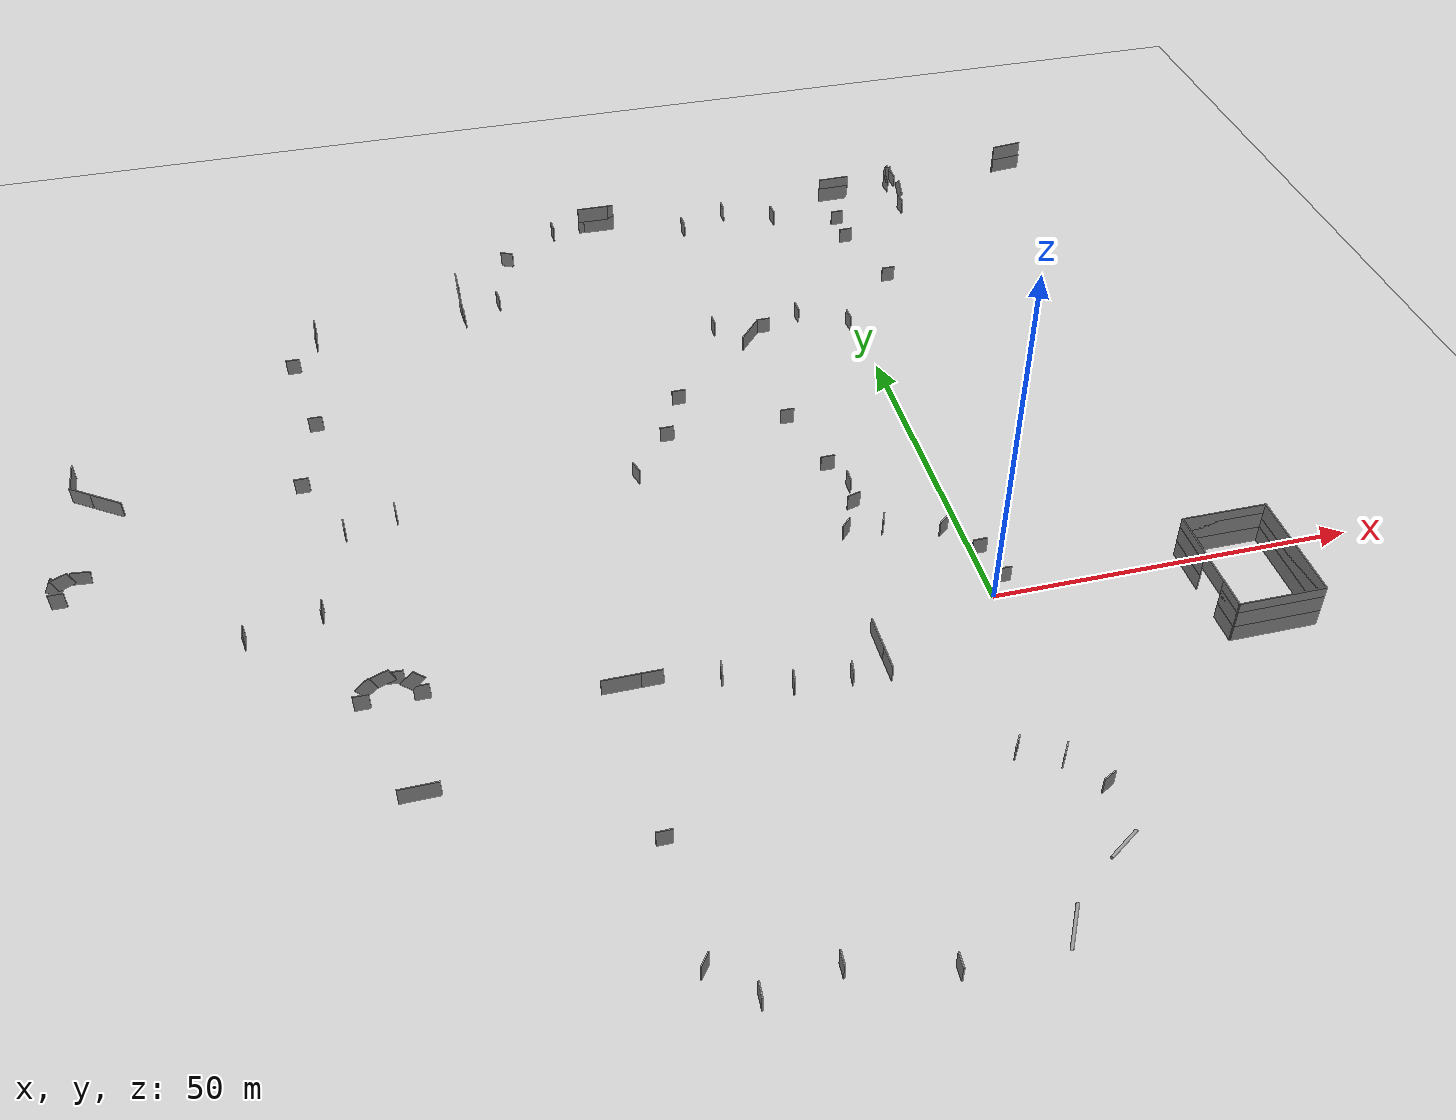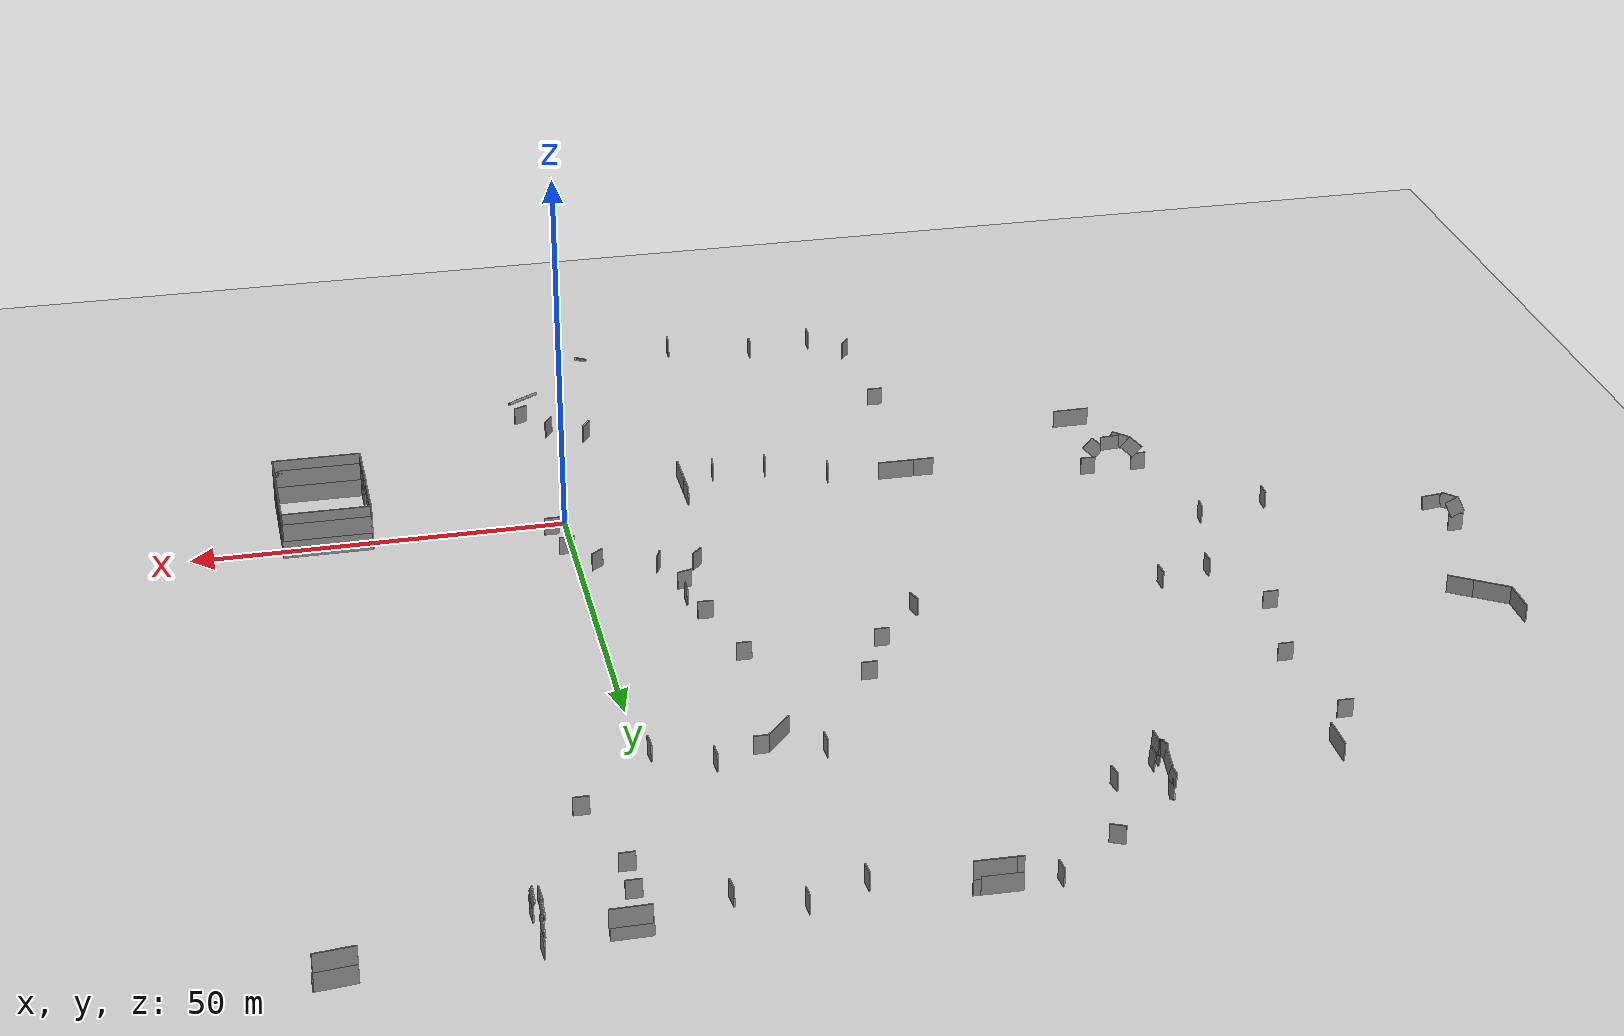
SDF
<sdf version="1.6">
 <world name="default">
  <light name="sun" type="directional">
   <pose>0 0 10 0 -0 0</pose>
   <diffuse>0.8 0.8 0.8 1</diffuse>
   <specular>0.2 0.2 0.2 1</specular>
   <attenuation>
    <range>1000</range>
    <constant>0.9</constant>
    <linear>0.01</linear>
    <quadratic>0.001</quadratic>
   </attenuation>
   <direction>-0.5 0.1 -0.9</direction>
  </light>
  <model name="ground_plane">
   <static>1</static>
   <link name="link">
    <collision name="collision">
     <geometry><plane><normal>0 0 1</normal><size>100 100</size></plane></geometry>
     <surface><friction><ode><mu>100</mu><mu2>50</mu2></ode></friction></surface>
    </collision>
    <visual name="visual">
     <cast_shadows>0</cast_shadows>
     <geometry><plane><normal>0 0 1</normal><size>100 100</size></plane></geometry>
     <material>
      <script><uri>file://media/materials/scripts/gazebo.material</uri><name>Gazebo/Grey</name></script>
     </material>
    </visual>
   </link>
  </model>
  <gravity>0 0 -9.8</gravity>
  <magnetic_field>6e-06 2.3e-05 -4.2e-05</magnetic_field>
  <atmosphere type="adiabatic"/>
  <physics name="default_physics" default="0" type="ode">
   <max_step_size>0.001</max_step_size>
   <real_time_factor>1</real_time_factor>
   <real_time_update_rate>1000</real_time_update_rate>
  </physics>
  <scene><ambient>0.4 0.4 0.4 1</ambient><background>0.7 0.7 0.7 1</background><shadows>1</shadows></scene>
  <audio><device>default</device></audio>
  <spherical_coordinates>
   <surface_model>EARTH_WGS84</surface_model>
   <latitude_deg>0</latitude_deg>
   <longitude_deg>0</longitude_deg>
   <elevation>0</elevation>
   <heading_deg>0</heading_deg>
  </spherical_coordinates>
  <model name="PaperTestTunnelHouse">
   <pose>31.9195 -6.3195 0 0 -0 0</pose>
   <link name="Wall_10">
    <collision name="Wall_10_Collision">
     <geometry><box><size>4.25 0.15 2.5</size></box></geometry>
     <pose>0 0 1.25 0 -0 0</pose>
    </collision>
    <visual name="Wall_10_Visual">
     <pose>0 0 1.25 0 -0 0</pose>
     <geometry><box><size>4.25 0.15 2.5</size></box></geometry>
     <material>
      <script><uri>file://media/materials/scripts/gazebo.material</uri><name>Gazebo/Grey</name></script>
      <ambient>1 1 1 1</ambient>
     </material>
     <meta><layer>0</layer></meta>
    </visual>
    <pose>-5.925 -5.875 0 0 -0 1.5708</pose>
   </link>
   <link name="Wall_6">
    <collision name="Wall_6_Collision">
     <geometry><box><size>6.75 0.15 2.5</size></box></geometry>
     <pose>0 0 1.25 0 -0 0</pose>
    </collision>
    <visual name="Wall_6_Visual">
     <pose>0 0 1.25 0 -0 0</pose>
     <geometry><box><size>6.75 0.15 2.5</size></box></geometry>
     <material>
      <script><uri>file://media/materials/scripts/gazebo.material</uri><name>Gazebo/Grey</name></script>
      <ambient>1 1 1 1</ambient>
     </material>
     <meta><layer>0</layer></meta>
    </visual>
    <pose>-5.925 4.625 0 0 -0 1.5708</pose>
   </link>
   <link name="Wall_7">
    <collision name="Wall_7_Collision">
     <geometry><box><size>12 0.15 2.5</size></box></geometry>
     <pose>0 0 1.25 0 -0 0</pose>
    </collision>
    <visual name="Wall_7_Visual">
     <pose>0 0 1.25 0 -0 0</pose>
     <geometry><box><size>12 0.15 2.5</size></box></geometry>
     <material>
      <script><uri>file://media/materials/scripts/gazebo.material</uri><name>Gazebo/Grey</name></script>
      <ambient>1 1 1 1</ambient>
     </material>
     <meta><layer>0</layer></meta>
    </visual>
    <pose>-0 7.925 0 0 -0 0</pose>
   </link>
   <link name="Wall_8">
    <collision name="Wall_8_Collision">
     <geometry><box><size>16 0.15 2.5</size></box></geometry>
     <pose>0 0 1.25 0 -0 0</pose>
    </collision>
    <visual name="Wall_8_Visual">
     <pose>0 0 1.25 0 -0 0</pose>
     <geometry><box><size>16 0.15 2.5</size></box></geometry>
     <material>
      <script><uri>file://media/materials/scripts/gazebo.material</uri><name>Gazebo/Grey</name></script>
      <ambient>1 1 1 1</ambient>
     </material>
     <meta><layer>0</layer></meta>
    </visual>
    <pose>5.925 0 0 0 -0 -1.5708</pose>
   </link>
   <link name="Wall_9">
    <collision name="Wall_9_Collision">
     <geometry><box><size>12 0.15 2.5</size></box></geometry>
     <pose>0 0 1.25 0 -0 0</pose>
    </collision>
    <visual name="Wall_9_Visual">
     <pose>0 0 1.25 0 -0 0</pose>
     <geometry><box><size>12 0.15 2.5</size></box></geometry>
     <material>
      <script><uri>file://media/materials/scripts/gazebo.material</uri><name>Gazebo/Grey</name></script>
      <ambient>1 1 1 1</ambient>
     </material>
     <meta><layer>0</layer></meta>
    </visual>
    <pose>-0 -7.925 0 0 -0 3.14159</pose>
   </link>
   <static>1</static>
  </model>
  <model name="PaperTestTunnelHouse_0">
   <pose>31.9195 -6.319 2.5 0 -0 0</pose>
   <link name="Wall_10">
    <collision name="Wall_10_Collision">
     <geometry><box><size>4.25 0.15 2.5</size></box></geometry>
     <pose>0 0 1.25 0 -0 0</pose>
    </collision>
    <visual name="Wall_10_Visual">
     <pose>0 0 1.25 0 -0 0</pose>
     <geometry><box><size>4.25 0.15 2.5</size></box></geometry>
     <material>
      <script><uri>file://media/materials/scripts/gazebo.material</uri><name>Gazebo/Grey</name></script>
      <ambient>1 1 1 1</ambient>
     </material>
     <meta><layer>0</layer></meta>
    </visual>
    <pose>-5.925 -5.875 0 0 -0 1.5708</pose>
   </link>
   <link name="Wall_6">
    <collision name="Wall_6_Collision">
     <geometry><box><size>6.75 0.15 2.5</size></box></geometry>
     <pose>0 0 1.25 0 -0 0</pose>
    </collision>
    <visual name="Wall_6_Visual">
     <pose>0 0 1.25 0 -0 0</pose>
     <geometry><box><size>6.75 0.15 2.5</size></box></geometry>
     <material>
      <script><uri>file://media/materials/scripts/gazebo.material</uri><name>Gazebo/Grey</name></script>
      <ambient>1 1 1 1</ambient>
     </material>
     <meta><layer>0</layer></meta>
    </visual>
    <pose>-5.925 4.625 0 0 -0 1.5708</pose>
   </link>
   <link name="Wall_7">
    <collision name="Wall_7_Collision">
     <geometry><box><size>12 0.15 2.5</size></box></geometry>
     <pose>0 0 1.25 0 -0 0</pose>
    </collision>
    <visual name="Wall_7_Visual">
     <pose>0 0 1.25 0 -0 0</pose>
     <geometry><box><size>12 0.15 2.5</size></box></geometry>
     <material>
      <script><uri>file://media/materials/scripts/gazebo.material</uri><name>Gazebo/Grey</name></script>
      <ambient>1 1 1 1</ambient>
     </material>
     <meta><layer>0</layer></meta>
    </visual>
    <pose>-0 7.925 0 0 -0 0</pose>
   </link>
   <link name="Wall_8">
    <collision name="Wall_8_Collision">
     <geometry><box><size>16 0.15 2.5</size></box></geometry>
     <pose>0 0 1.25 0 -0 0</pose>
    </collision>
    <visual name="Wall_8_Visual">
     <pose>0 0 1.25 0 -0 0</pose>
     <geometry><box><size>16 0.15 2.5</size></box></geometry>
     <material>
      <script><uri>file://media/materials/scripts/gazebo.material</uri><name>Gazebo/Grey</name></script>
      <ambient>1 1 1 1</ambient>
     </material>
     <meta><layer>0</layer></meta>
    </visual>
    <pose>5.925 0 0 0 -0 -1.5708</pose>
   </link>
   <link name="Wall_9">
    <collision name="Wall_9_Collision">
     <geometry><box><size>12 0.15 2.5</size></box></geometry>
     <pose>0 0 1.25 0 -0 0</pose>
    </collision>
    <visual name="Wall_9_Visual">
     <pose>0 0 1.25 0 -0 0</pose>
     <geometry><box><size>12 0.15 2.5</size></box></geometry>
     <material>
      <script><uri>file://media/materials/scripts/gazebo.material</uri><name>Gazebo/Grey</name></script>
      <ambient>1 1 1 1</ambient>
     </material>
     <meta><layer>0</layer></meta>
    </visual>
    <pose>-0 -7.925 0 0 -0 3.14159</pose>
   </link>
   <static>1</static>
  </model>
  <model name="5mWall">
   <pose>25.971 -7.56033 4 0 -0 0</pose>
   <link name="Wall_0">
    <collision name="Wall_0_Collision">
     <geometry><box><size>5 0.15 2.5</size></box></geometry>
     <pose>0 0 1.25 0 -0 0</pose>
    </collision>
    <visual name="Wall_0_Visual">
     <pose>0 0 1.25 0 -0 0</pose>
     <geometry><box><size>5 0.15 2.5</size></box></geometry>
     <material>
      <script><uri>file://media/materials/scripts/gazebo.material</uri><name>Gazebo/Grey</name></script>
      <ambient>1 1 1 1</ambient>
     </material>
     <meta><layer>0</layer></meta>
    </visual>
    <pose>0 -0 0 0 -0 1.5708</pose>
   </link>
   <static>1</static>
  </model>
  <model name="PaperTestTunnelHouse_1">
   <pose>31.9195 -6.319 4 0 -0 0</pose>
   <link name="Wall_10">
    <collision name="Wall_10_Collision">
     <geometry><box><size>4.25 0.15 2.5</size></box></geometry>
     <pose>0 0 1.25 0 -0 0</pose>
    </collision>
    <visual name="Wall_10_Visual">
     <pose>0 0 1.25 0 -0 0</pose>
     <geometry><box><size>4.25 0.15 2.5</size></box></geometry>
     <material>
      <script><uri>file://media/materials/scripts/gazebo.material</uri><name>Gazebo/Grey</name></script>
      <ambient>1 1 1 1</ambient>
     </material>
     <meta><layer>0</layer></meta>
    </visual>
    <pose>-5.925 -5.875 0 0 -0 1.5708</pose>
   </link>
   <link name="Wall_6">
    <collision name="Wall_6_Collision">
     <geometry><box><size>6.75 0.15 2.5</size></box></geometry>
     <pose>0 0 1.25 0 -0 0</pose>
    </collision>
    <visual name="Wall_6_Visual">
     <pose>0 0 1.25 0 -0 0</pose>
     <geometry><box><size>6.75 0.15 2.5</size></box></geometry>
     <material>
      <script><uri>file://media/materials/scripts/gazebo.material</uri><name>Gazebo/Grey</name></script>
      <ambient>1 1 1 1</ambient>
     </material>
     <meta><layer>0</layer></meta>
    </visual>
    <pose>-5.925 4.625 0 0 -0 1.5708</pose>
   </link>
   <link name="Wall_7">
    <collision name="Wall_7_Collision">
     <geometry><box><size>12 0.15 2.5</size></box></geometry>
     <pose>0 0 1.25 0 -0 0</pose>
    </collision>
    <visual name="Wall_7_Visual">
     <pose>0 0 1.25 0 -0 0</pose>
     <geometry><box><size>12 0.15 2.5</size></box></geometry>
     <material>
      <script><uri>file://media/materials/scripts/gazebo.material</uri><name>Gazebo/Grey</name></script>
      <ambient>1 1 1 1</ambient>
     </material>
     <meta><layer>0</layer></meta>
    </visual>
    <pose>-0 7.925 0 0 -0 0</pose>
   </link>
   <link name="Wall_8">
    <collision name="Wall_8_Collision">
     <geometry><box><size>16 0.15 2.5</size></box></geometry>
     <pose>0 0 1.25 0 -0 0</pose>
    </collision>
    <visual name="Wall_8_Visual">
     <pose>0 0 1.25 0 -0 0</pose>
     <geometry><box><size>16 0.15 2.5</size></box></geometry>
     <material>
      <script><uri>file://media/materials/scripts/gazebo.material</uri><name>Gazebo/Grey</name></script>
      <ambient>1 1 1 1</ambient>
     </material>
     <meta><layer>0</layer></meta>
    </visual>
    <pose>5.925 0 0 0 -0 -1.5708</pose>
   </link>
   <link name="Wall_9">
    <collision name="Wall_9_Collision">
     <geometry><box><size>12 0.15 2.5</size></box></geometry>
     <pose>0 0 1.25 0 -0 0</pose>
    </collision>
    <visual name="Wall_9_Visual">
     <pose>0 0 1.25 0 -0 0</pose>
     <geometry><box><size>12 0.15 2.5</size></box></geometry>
     <material>
      <script><uri>file://media/materials/scripts/gazebo.material</uri><name>Gazebo/Grey</name></script>
      <ambient>1 1 1 1</ambient>
     </material>
     <meta><layer>0</layer></meta>
    </visual>
    <pose>-0 -7.925 0 0 -0 3.14159</pose>
   </link>
   <static>1</static>
  </model>
  <model name="empty_pillar_1">
   <link name="link">
    <inertial>
     <mass>1</mass>
     <inertia><ixx>0.145833</ixx><ixy>0</ixy><ixz>0</ixz><iyy>0.145833</iyy><iyz>0</iyz><izz>0.125</izz></inertia>
    </inertial>
    <visual name="visual">
     <geometry><cylinder><radius>0.2</radius><length>5</length></cylinder></geometry>
     <material>
      <script><name>Gazebo/Grey</name><uri>file://media/materials/scripts/gazebo.material</uri></script>
      <shader type="vertex"><normal_map>__default__</normal_map></shader>
      <ambient>0.3 0.3 0.3 1</ambient>
      <diffuse>0.7 0.7 0.7 1</diffuse>
      <specular>0.01 0.01 0.01 1</specular>
      <emissive>0 0 0 1</emissive>
     </material>
    </visual>
    <collision name="collision">
     <geometry><cylinder><radius>0.05</radius><length>5</length></cylinder></geometry>
     <surface>
      <friction>
       <ode><mu>1</mu><mu2>1</mu2><fdir1>0 0 0</fdir1><slip1>0</slip1><slip2>0</slip2></ode>
       <torsional>
        <coefficient>1</coefficient>
        <patch_radius>0</patch_radius>
        <surface_radius>0</surface_radius>
        <use_patch_radius>1</use_patch_radius>
        <ode><slip>0</slip></ode>
       </torsional>
      </friction>
      <bounce><restitution_coefficient>0</restitution_coefficient><threshold>1e+06</threshold></bounce>
      <contact>
       <collide_without_contact>0</collide_without_contact>
       <collide_without_contact_bitmask>1</collide_without_contact_bitmask>
       <collide_bitmask>1</collide_bitmask>
       <ode>
        <soft_cfm>0</soft_cfm>
        <soft_erp>0.2</soft_erp>
        <kp>1e+13</kp>
        <kd>1</kd>
        <max_vel>0.01</max_vel>
        <min_depth>0</min_depth>
       </ode>
       <bullet>
        <split_impulse>1</split_impulse>
        <split_impulse_penetration_threshold>-0.01</split_impulse_penetration_threshold>
        <soft_cfm>0</soft_cfm>
        <soft_erp>0.2</soft_erp>
        <kp>1e+13</kp>
        <kd>1</kd>
       </bullet>
      </contact>
     </surface>
    </collision>
   </link>
   <static>0</static>
   <pose>0.363146 -39.6227 0.049992 -1.5708 0.874181 2.14691</pose>
  </model>
  <model name="empty_pillar_2">
   <link name="link">
    <inertial>
     <mass>1</mass>
     <inertia><ixx>0.145833</ixx><ixy>0</ixy><ixz>0</ixz><iyy>0.145833</iyy><iyz>0</iyz><izz>0.125</izz></inertia>
    </inertial>
    <visual name="visual">
     <geometry><cylinder><radius>0.2</radius><length>5</length></cylinder></geometry>
     <material>
      <script><name>Gazebo/Grey</name><uri>file://media/materials/scripts/gazebo.material</uri></script>
      <shader type="vertex"><normal_map>__default__</normal_map></shader>
      <ambient>0.3 0.3 0.3 1</ambient>
      <diffuse>0.7 0.7 0.7 1</diffuse>
      <specular>0.01 0.01 0.01 1</specular>
      <emissive>0 0 0 1</emissive>
     </material>
    </visual>
    <collision name="collision">
     <geometry><cylinder><radius>0.05</radius><length>5</length></cylinder></geometry>
     <surface>
      <friction>
       <ode><mu>1</mu><mu2>1</mu2><fdir1>0 0 0</fdir1><slip1>0</slip1><slip2>0</slip2></ode>
       <torsional>
        <coefficient>1</coefficient>
        <patch_radius>0</patch_radius>
        <surface_radius>0</surface_radius>
        <use_patch_radius>1</use_patch_radius>
        <ode><slip>0</slip></ode>
       </torsional>
      </friction>
      <bounce><restitution_coefficient>0</restitution_coefficient><threshold>1e+06</threshold></bounce>
      <contact>
       <collide_without_contact>0</collide_without_contact>
       <collide_without_contact_bitmask>1</collide_without_contact_bitmask>
       <collide_bitmask>1</collide_bitmask>
       <ode>
        <soft_cfm>0</soft_cfm>
        <soft_erp>0.2</soft_erp>
        <kp>1e+13</kp>
        <kd>1</kd>
        <max_vel>0.01</max_vel>
        <min_depth>0</min_depth>
       </ode>
       <bullet>
        <split_impulse>1</split_impulse>
        <split_impulse_penetration_threshold>-0.01</split_impulse_penetration_threshold>
        <soft_cfm>0</soft_cfm>
        <soft_erp>0.2</soft_erp>
        <kp>1e+13</kp>
        <kd>1</kd>
       </bullet>
      </contact>
     </surface>
    </collision>
   </link>
   <static>0</static>
   <pose>-9.55732 -48.7408 1.20133 -0.794834 0.84896 0.163453</pose>
  </model>
  <model name="2mWall_3">
   <pose>2.10228 2.41901 0 0 -0 0</pose>
   <link name="Wall_0">
    <collision name="Wall_0_Collision">
     <geometry><box><size>2 0.15 2.5</size></box></geometry>
     <pose>0 0 1.25 0 -0 0</pose>
    </collision>
    <visual name="Wall_0_Visual">
     <pose>0 0 1.25 0 -0 0</pose>
     <geometry><box><size>2 0.15 2.5</size></box></geometry>
     <material>
      <script><uri>file://media/materials/scripts/gazebo.material</uri><name>Gazebo/Grey</name></script>
      <ambient>1 1 1 1</ambient>
     </material>
     <meta><layer>0</layer></meta>
    </visual>
   </link>
   <static>1</static>
  </model>
  <model name="2mWall_4">
   <pose>-10.1702 15.3219 0 0 -0 1.16983</pose>
   <link name="Wall_0">
    <collision name="Wall_0_Collision">
     <geometry><box><size>2 0.15 2.5</size></box></geometry>
     <pose>0 0 1.25 0 -0 0</pose>
    </collision>
    <visual name="Wall_0_Visual">
     <pose>0 0 1.25 0 -0 0</pose>
     <geometry><box><size>2 0.15 2.5</size></box></geometry>
     <material>
      <script><uri>file://media/materials/scripts/gazebo.material</uri><name>Gazebo/Grey</name></script>
      <ambient>1 1 1 1</ambient>
     </material>
     <meta><layer>0</layer></meta>
    </visual>
   </link>
   <static>1</static>
  </model>
  <model name="2mWall_5">
   <pose>-83.1544 54.943 0 0 -0 0</pose>
   <link name="Wall_0">
    <collision name="Wall_0_Collision">
     <geometry><box><size>2 0.15 2.5</size></box></geometry>
     <pose>0 0 1.25 0 -0 0</pose>
    </collision>
    <visual name="Wall_0_Visual">
     <pose>0 0 1.25 0 -0 0</pose>
     <geometry><box><size>2 0.15 2.5</size></box></geometry>
     <material>
      <script><uri>file://media/materials/scripts/gazebo.material</uri><name>Gazebo/Grey</name></script>
      <ambient>1 1 1 1</ambient>
     </material>
     <meta><layer>0</layer></meta>
    </visual>
   </link>
   <static>1</static>
  </model>
  <model name="2mWall_6">
   <pose>-85.7141 69.513 0 0 -0 0</pose>
   <link name="Wall_0">
    <collision name="Wall_0_Collision">
     <geometry><box><size>2 0.15 2.5</size></box></geometry>
     <pose>0 0 1.25 0 -0 0</pose>
    </collision>
    <visual name="Wall_0_Visual">
     <pose>0 0 1.25 0 -0 0</pose>
     <geometry><box><size>2 0.15 2.5</size></box></geometry>
     <material>
      <script><uri>file://media/materials/scripts/gazebo.material</uri><name>Gazebo/Grey</name></script>
      <ambient>1 1 1 1</ambient>
     </material>
     <meta><layer>0</layer></meta>
    </visual>
   </link>
   <static>1</static>
  </model>
  <model name="2mWall_7">
   <pose>-49.3322 -27.3207 0 0 -0 0</pose>
   <link name="Wall_0">
    <collision name="Wall_0_Collision">
     <geometry><box><size>2 0.15 2.5</size></box></geometry>
     <pose>0 0 1.25 0 -0 0</pose>
    </collision>
    <visual name="Wall_0_Visual">
     <pose>0 0 1.25 0 -0 0</pose>
     <geometry><box><size>2 0.15 2.5</size></box></geometry>
     <material>
      <script><uri>file://media/materials/scripts/gazebo.material</uri><name>Gazebo/Grey</name></script>
      <ambient>1 1 1 1</ambient>
     </material>
     <meta><layer>0</layer></meta>
    </visual>
   </link>
   <static>1</static>
  </model>
  <model name="2mWall_8">
   <pose>-59.4366 74.776 2.05199 -1.44233 1.49736 0.210842</pose>
   <link name="Wall_0">
    <collision name="Wall_0_Collision">
     <geometry><box><size>2 0.15 2.5</size></box></geometry>
     <pose>0 0 1.25 0 -0 0</pose>
    </collision>
    <visual name="Wall_0_Visual">
     <pose>0 0 1.25 0 -0 0</pose>
     <geometry><box><size>2 0.15 2.5</size></box></geometry>
     <material>
      <script><uri>file://media/materials/scripts/gazebo.material</uri><name>Gazebo/Grey</name></script>
      <ambient>1 1 1 1</ambient>
     </material>
     <meta><layer>0</layer></meta>
    </visual>
   </link>
   <static>1</static>
  </model>
  <model name="2mWall_8_clone">
   <pose>-59.4772 74.6594 3.48956 0.884504 -1.49033 -2.45689</pose>
   <link name="Wall_0">
    <collision name="Wall_0_Collision">
     <geometry><box><size>2 0.15 2.5</size></box></geometry>
     <pose>0 0 1.25 0 -0 0</pose>
    </collision>
    <visual name="Wall_0_Visual">
     <pose>0 0 1.25 0 -0 0</pose>
     <geometry><box><size>2 0.15 2.5</size></box></geometry>
     <material>
      <script><uri>file://media/materials/scripts/gazebo.material</uri><name>Gazebo/Grey</name></script>
      <ambient>1 1 1 1</ambient>
     </material>
     <meta><layer>0</layer></meta>
    </visual>
   </link>
   <static>1</static>
  </model>
  <model name="2mWall_8_clone_clone">
   <pose>-59.433 81.5822 3.12252 0.884504 -1.49033 -2.45689</pose>
   <link name="Wall_0">
    <collision name="Wall_0_Collision">
     <geometry><box><size>2 0.15 2.5</size></box></geometry>
     <pose>0 0 1.25 0 -0 0</pose>
    </collision>
    <visual name="Wall_0_Visual">
     <pose>0 0 1.25 0 -0 0</pose>
     <geometry><box><size>2 0.15 2.5</size></box></geometry>
     <material>
      <script><uri>file://media/materials/scripts/gazebo.material</uri><name>Gazebo/Grey</name></script>
      <ambient>1 1 1 1</ambient>
     </material>
     <meta><layer>0</layer></meta>
    </visual>
   </link>
   <static>1</static>
  </model>
  <model name="2mWall_8_clone_clone_0">
   <pose>-59.4212 82.3391 2.57822 3.07188 -0.522352 1.56761</pose>
   <link name="Wall_0">
    <collision name="Wall_0_Collision">
     <geometry><box><size>2 0.15 2.5</size></box></geometry>
     <pose>0 0 1.25 0 -0 0</pose>
    </collision>
    <visual name="Wall_0_Visual">
     <pose>0 0 1.25 0 -0 0</pose>
     <geometry><box><size>2 0.15 2.5</size></box></geometry>
     <material>
      <script><uri>file://media/materials/scripts/gazebo.material</uri><name>Gazebo/Grey</name></script>
      <ambient>1 1 1 1</ambient>
     </material>
     <meta><layer>0</layer></meta>
    </visual>
   </link>
   <static>1</static>
  </model>
  <model name="2mWall_8_clone_clone_1">
   <pose>-59.5208 77.8778 3.96696 0.167942 -1.18963 -1.73007</pose>
   <link name="Wall_0">
    <collision name="Wall_0_Collision">
     <geometry><box><size>2 0.15 2.5</size></box></geometry>
     <pose>0 0 1.25 0 -0 0</pose>
    </collision>
    <visual name="Wall_0_Visual">
     <pose>0 0 1.25 0 -0 0</pose>
     <geometry><box><size>2 0.15 2.5</size></box></geometry>
     <material>
      <script><uri>file://media/materials/scripts/gazebo.material</uri><name>Gazebo/Grey</name></script>
      <ambient>1 1 1 1</ambient>
     </material>
     <meta><layer>0</layer></meta>
    </visual>
   </link>
   <static>1</static>
  </model>
  <model name="2mWall_8_clone_clone_1_clone">
   <pose>-59.4971 79.625 4.29051 2.97056 -1.19679 1.72703</pose>
   <link name="Wall_0">
    <collision name="Wall_0_Collision">
     <geometry><box><size>2 0.15 2.5</size></box></geometry>
     <pose>0 0 1.25 0 -0 0</pose>
    </collision>
    <visual name="Wall_0_Visual">
     <pose>0 0 1.25 0 -0 0</pose>
     <geometry><box><size>2 0.15 2.5</size></box></geometry>
     <material>
      <script><uri>file://media/materials/scripts/gazebo.material</uri><name>Gazebo/Grey</name></script>
      <ambient>1 1 1 1</ambient>
     </material>
     <meta><layer>0</layer></meta>
    </visual>
   </link>
   <static>1</static>
  </model>
  <model name="2mWall_10">
   <pose>17.241 91.132 0 0 0 -1.5162</pose>
   <link name="Wall_0">
    <collision name="Wall_0_Collision">
     <geometry><box><size>2 0.15 2.5</size></box></geometry>
     <pose>0 0 1.25 0 -0 0</pose>
    </collision>
    <visual name="Wall_0_Visual">
     <pose>0 0 1.25 0 -0 0</pose>
     <geometry><box><size>2 0.15 2.5</size></box></geometry>
     <material>
      <script><uri>file://media/materials/scripts/gazebo.material</uri><name>Gazebo/Grey</name></script>
      <ambient>1 1 1 1</ambient>
     </material>
     <meta><layer>0</layer></meta>
    </visual>
   </link>
   <static>1</static>
  </model>
  <model name="2mWall_10_clone">
   <pose>16.9834 98.3399 0 0 0 -1.5162</pose>
   <link name="Wall_0">
    <collision name="Wall_0_Collision">
     <geometry><box><size>2 0.15 2.5</size></box></geometry>
     <pose>0 0 1.25 0 -0 0</pose>
    </collision>
    <visual name="Wall_0_Visual">
     <pose>0 0 1.25 0 -0 0</pose>
     <geometry><box><size>2 0.15 2.5</size></box></geometry>
     <material>
      <script><uri>file://media/materials/scripts/gazebo.material</uri><name>Gazebo/Grey</name></script>
      <ambient>1 1 1 1</ambient>
     </material>
     <meta><layer>0</layer></meta>
    </visual>
   </link>
   <static>1</static>
  </model>
  <model name="2mWall_10_clone_0">
   <pose>16.8368 98.3987 2.26777 0 0.520041 -1.5162</pose>
   <link name="Wall_0">
    <collision name="Wall_0_Collision">
     <geometry><box><size>2 0.15 2.5</size></box></geometry>
     <pose>0 0 1.25 0 -0 0</pose>
    </collision>
    <visual name="Wall_0_Visual">
     <pose>0 0 1.25 0 -0 0</pose>
     <geometry><box><size>2 0.15 2.5</size></box></geometry>
     <material>
      <script><uri>file://media/materials/scripts/gazebo.material</uri><name>Gazebo/Grey</name></script>
      <ambient>1 1 1 1</ambient>
     </material>
     <meta><layer>0</layer></meta>
    </visual>
   </link>
   <static>1</static>
  </model>
  <model name="2mWall_10_clone_0_clone">
   <pose>17.2796 91.409 2.64511 -0 -0.760861 -1.5162</pose>
   <link name="Wall_0">
    <collision name="Wall_0_Collision">
     <geometry><box><size>2 0.15 2.5</size></box></geometry>
     <pose>0 0 1.25 0 -0 0</pose>
    </collision>
    <visual name="Wall_0_Visual">
     <pose>0 0 1.25 0 -0 0</pose>
     <geometry><box><size>2 0.15 2.5</size></box></geometry>
     <material>
      <script><uri>file://media/materials/scripts/gazebo.material</uri><name>Gazebo/Grey</name></script>
      <ambient>1 1 1 1</ambient>
     </material>
     <meta><layer>0</layer></meta>
    </visual>
   </link>
   <static>1</static>
  </model>
  <model name="2mWall_10_clone_0_clone_clone">
   <pose>16.5072 95.6413 4.55309 4e-06 1.56464 -1.5162</pose>
   <link name="Wall_0">
    <collision name="Wall_0_Collision">
     <geometry><box><size>2 0.15 2.5</size></box></geometry>
     <pose>0 0 1.25 0 -0 0</pose>
    </collision>
    <visual name="Wall_0_Visual">
     <pose>0 0 1.25 0 -0 0</pose>
     <geometry><box><size>2 0.15 2.5</size></box></geometry>
     <material>
      <script><uri>file://media/materials/scripts/gazebo.material</uri><name>Gazebo/Grey</name></script>
      <ambient>1 1 1 1</ambient>
     </material>
     <meta><layer>0</layer></meta>
    </visual>
   </link>
   <static>1</static>
  </model>
  <model name="2mWall_10_clone_0_clone_clone_clone">
   <pose>16.5894 97.3522 3.74124 -0 0.981697 -1.5162</pose>
   <link name="Wall_0">
    <collision name="Wall_0_Collision">
     <geometry><box><size>2 0.15 2.5</size></box></geometry>
     <pose>0 0 1.25 0 -0 0</pose>
    </collision>
    <visual name="Wall_0_Visual">
     <pose>0 0 1.25 0 -0 0</pose>
     <geometry><box><size>2 0.15 2.5</size></box></geometry>
     <material>
      <script><uri>file://media/materials/scripts/gazebo.material</uri><name>Gazebo/Grey</name></script>
      <ambient>1 1 1 1</ambient>
     </material>
     <meta><layer>0</layer></meta>
    </visual>
   </link>
   <static>1</static>
  </model>
  <model name="2mWall_11">
   <pose>-80.5459 0.435841 0 0 -0 0</pose>
   <link name="Wall_0">
    <collision name="Wall_0_Collision">
     <geometry><box><size>2 0.15 2.5</size></box></geometry>
     <pose>0 0 1.25 0 -0 0</pose>
    </collision>
    <visual name="Wall_0_Visual">
     <pose>0 0 1.25 0 -0 0</pose>
     <geometry><box><size>2 0.15 2.5</size></box></geometry>
     <material>
      <script><uri>file://media/materials/scripts/gazebo.material</uri><name>Gazebo/Grey</name></script>
      <ambient>1 1 1 1</ambient>
     </material>
     <meta><layer>0</layer></meta>
    </visual>
   </link>
   <static>1</static>
  </model>
  <model name="2mWall_11_clone">
   <pose>-73.3311 0.380501 0 0 -0 0</pose>
   <link name="Wall_0">
    <collision name="Wall_0_Collision">
     <geometry><box><size>2 0.15 2.5</size></box></geometry>
     <pose>0 0 1.25 0 -0 0</pose>
    </collision>
    <visual name="Wall_0_Visual">
     <pose>0 0 1.25 0 -0 0</pose>
     <geometry><box><size>2 0.15 2.5</size></box></geometry>
     <material>
      <script><uri>file://media/materials/scripts/gazebo.material</uri><name>Gazebo/Grey</name></script>
      <ambient>1 1 1 1</ambient>
     </material>
     <meta><layer>0</layer></meta>
    </visual>
   </link>
   <static>1</static>
  </model>
  <model name="2mWall_11_clone_0">
   <pose>-80.3991 0.506506 2.684 0 0.816528 0</pose>
   <link name="Wall_0">
    <collision name="Wall_0_Collision">
     <geometry><box><size>2 0.15 2.5</size></box></geometry>
     <pose>0 0 1.25 0 -0 0</pose>
    </collision>
    <visual name="Wall_0_Visual">
     <pose>0 0 1.25 0 -0 0</pose>
     <geometry><box><size>2 0.15 2.5</size></box></geometry>
     <material>
      <script><uri>file://media/materials/scripts/gazebo.material</uri><name>Gazebo/Grey</name></script>
      <ambient>1 1 1 1</ambient>
     </material>
     <meta><layer>0</layer></meta>
    </visual>
   </link>
   <static>1</static>
  </model>
  <model name="2mWall_11_clone_0_clone">
   <pose>-75.059 0.119832 2.90318 0 0.816528 0</pose>
   <link name="Wall_0">
    <collision name="Wall_0_Collision">
     <geometry><box><size>2 0.15 2.5</size></box></geometry>
     <pose>0 0 1.25 0 -0 0</pose>
    </collision>
    <visual name="Wall_0_Visual">
     <pose>0 0 1.25 0 -0 0</pose>
     <geometry><box><size>2 0.15 2.5</size></box></geometry>
     <material>
      <script><uri>file://media/materials/scripts/gazebo.material</uri><name>Gazebo/Grey</name></script>
      <ambient>1 1 1 1</ambient>
     </material>
     <meta><layer>0</layer></meta>
    </visual>
   </link>
   <static>1</static>
  </model>
  <model name="2mWall_11_clone_0_clone_0">
   <pose>-77.5474 0.489779 4.61692 3.14159 1.52824 3.14159</pose>
   <link name="Wall_0">
    <collision name="Wall_0_Collision">
     <geometry><box><size>2 0.15 2.5</size></box></geometry>
     <pose>0 0 1.25 0 -0 0</pose>
    </collision>
    <visual name="Wall_0_Visual">
     <pose>0 0 1.25 0 -0 0</pose>
     <geometry><box><size>2 0.15 2.5</size></box></geometry>
     <material>
      <script><uri>file://media/materials/scripts/gazebo.material</uri><name>Gazebo/Grey</name></script>
      <ambient>1 1 1 1</ambient>
     </material>
     <meta><layer>0</layer></meta>
    </visual>
   </link>
   <static>1</static>
  </model>
  <model name="2mWall_11_clone_0_clone_0_clone">
   <pose>-78.6518 0.388218 4.2827 0 1.18388 0</pose>
   <link name="Wall_0">
    <collision name="Wall_0_Collision">
     <geometry><box><size>2 0.15 2.5</size></box></geometry>
     <pose>0 0 1.25 0 -0 0</pose>
    </collision>
    <visual name="Wall_0_Visual">
     <pose>0 0 1.25 0 -0 0</pose>
     <geometry><box><size>2 0.15 2.5</size></box></geometry>
     <material>
      <script><uri>file://media/materials/scripts/gazebo.material</uri><name>Gazebo/Grey</name></script>
      <ambient>1 1 1 1</ambient>
     </material>
     <meta><layer>0</layer></meta>
    </visual>
   </link>
   <static>1</static>
  </model>
  <model name="2mWall_12">
   <pose>-117.061 26.7716 0 0 -0 0</pose>
   <link name="Wall_0">
    <collision name="Wall_0_Collision">
     <geometry><box><size>2 0.15 2.5</size></box></geometry>
     <pose>0 0 1.25 0 -0 0</pose>
    </collision>
    <visual name="Wall_0_Visual">
     <pose>0 0 1.25 0 -0 0</pose>
     <geometry><box><size>2 0.15 2.5</size></box></geometry>
     <material>
      <script><uri>file://media/materials/scripts/gazebo.material</uri><name>Gazebo/Grey</name></script>
      <ambient>1 1 1 1</ambient>
     </material>
     <meta><layer>0</layer></meta>
    </visual>
   </link>
   <static>1</static>
  </model>
  <model name="2mWall_12_clone">
   <pose>-117.255 26.9303 2.48061 0 0.459908 0</pose>
   <link name="Wall_0">
    <collision name="Wall_0_Collision">
     <geometry><box><size>2 0.15 2.5</size></box></geometry>
     <pose>0 0 1.25 0 -0 0</pose>
    </collision>
    <visual name="Wall_0_Visual">
     <pose>0 0 1.25 0 -0 0</pose>
     <geometry><box><size>2 0.15 2.5</size></box></geometry>
     <material>
      <script><uri>file://media/materials/scripts/gazebo.material</uri><name>Gazebo/Grey</name></script>
      <ambient>1 1 1 1</ambient>
     </material>
     <meta><layer>0</layer></meta>
    </visual>
   </link>
   <static>1</static>
  </model>
  <model name="2mWall_12_clone_clone">
   <pose>-116.718 26.6567 3.99857 0 1.18222 0</pose>
   <link name="Wall_0">
    <collision name="Wall_0_Collision">
     <geometry><box><size>2 0.15 2.5</size></box></geometry>
     <pose>0 0 1.25 0 -0 0</pose>
    </collision>
    <visual name="Wall_0_Visual">
     <pose>0 0 1.25 0 -0 0</pose>
     <geometry><box><size>2 0.15 2.5</size></box></geometry>
     <material>
      <script><uri>file://media/materials/scripts/gazebo.material</uri><name>Gazebo/Grey</name></script>
      <ambient>1 1 1 1</ambient>
     </material>
     <meta><layer>0</layer></meta>
    </visual>
   </link>
   <static>1</static>
  </model>
  <model name="2mWall_12_clone_clone_clone">
   <pose>-114.552 26.6972 4.77087 3.14159 1.46985 3.14159</pose>
   <link name="Wall_0">
    <collision name="Wall_0_Collision">
     <geometry><box><size>2 0.15 2.5</size></box></geometry>
     <pose>0 0 1.25 0 -0 0</pose>
    </collision>
    <visual name="Wall_0_Visual">
     <pose>0 0 1.25 0 -0 0</pose>
     <geometry><box><size>2 0.15 2.5</size></box></geometry>
     <material>
      <script><uri>file://media/materials/scripts/gazebo.material</uri><name>Gazebo/Grey</name></script>
      <ambient>1 1 1 1</ambient>
     </material>
     <meta><layer>0</layer></meta>
    </visual>
   </link>
   <static>1</static>
  </model>
  <model name="2mWall">
   <pose>-34.7664 -47.2587 0 0 -0 1.51711</pose>
   <link name="Wall_0">
    <collision name="Wall_0_Collision">
     <geometry><box><size>2 0.15 2.5</size></box></geometry>
     <pose>0 0 1.25 0 -0 0</pose>
    </collision>
    <visual name="Wall_0_Visual">
     <pose>0 0 1.25 0 -0 0</pose>
     <geometry><box><size>2 0.15 2.5</size></box></geometry>
     <material>
      <script><uri>file://media/materials/scripts/gazebo.material</uri><name>Gazebo/Grey</name></script>
      <ambient>1 1 1 1</ambient>
     </material>
     <meta><layer>0</layer></meta>
    </visual>
   </link>
   <static>1</static>
  </model>
  <model name="2mWall_clone">
   <pose>-22.9675 -50.415 0 0 -0 1.51711</pose>
   <link name="Wall_0">
    <collision name="Wall_0_Collision">
     <geometry><box><size>2 0.15 2.5</size></box></geometry>
     <pose>0 0 1.25 0 -0 0</pose>
    </collision>
    <visual name="Wall_0_Visual">
     <pose>0 0 1.25 0 -0 0</pose>
     <geometry><box><size>2 0.15 2.5</size></box></geometry>
     <material>
      <script><uri>file://media/materials/scripts/gazebo.material</uri><name>Gazebo/Grey</name></script>
      <ambient>1 1 1 1</ambient>
     </material>
     <meta><layer>0</layer></meta>
    </visual>
   </link>
   <static>1</static>
  </model>
  <model name="2mWall_13">
   <pose>-22.0151 64.3612 -0.060612 0.000608 0.017278 1.60597</pose>
   <link name="Wall_0">
    <collision name="Wall_0_Collision">
     <geometry><box><size>2 0.15 2.5</size></box></geometry>
     <pose>0 0 1.25 0 -0 0</pose>
    </collision>
    <visual name="Wall_0_Visual">
     <pose>0 0 1.25 0 -0 0</pose>
     <geometry><box><size>2 0.15 2.5</size></box></geometry>
     <material>
      <script><uri>file://media/materials/scripts/gazebo.material</uri><name>Gazebo/Grey</name></script>
      <ambient>1 1 1 1</ambient>
     </material>
     <meta><layer>0</layer></meta>
    </visual>
   </link>
   <static>1</static>
  </model>
  <model name="2mWall_14">
   <pose>8.69558 71.5734 0 0 -0 0</pose>
   <link name="Wall_0">
    <collision name="Wall_0_Collision">
     <geometry><box><size>2 0.15 2.5</size></box></geometry>
     <pose>0 0 1.25 0 -0 0</pose>
    </collision>
    <visual name="Wall_0_Visual">
     <pose>0 0 1.25 0 -0 0</pose>
     <geometry><box><size>2 0.15 2.5</size></box></geometry>
     <material>
      <script><uri>file://media/materials/scripts/gazebo.material</uri><name>Gazebo/Grey</name></script>
      <ambient>1 1 1 1</ambient>
     </material>
     <meta><layer>0</layer></meta>
    </visual>
   </link>
   <static>1</static>
  </model>
  <model name="2mWall_15">
   <pose>5.3512 84.1095 0 0 -0 0</pose>
   <link name="Wall_0">
    <collision name="Wall_0_Collision">
     <geometry><box><size>2 0.15 2.5</size></box></geometry>
     <pose>0 0 1.25 0 -0 0</pose>
    </collision>
    <visual name="Wall_0_Visual">
     <pose>0 0 1.25 0 -0 0</pose>
     <geometry><box><size>2 0.15 2.5</size></box></geometry>
     <material>
      <script><uri>file://media/materials/scripts/gazebo.material</uri><name>Gazebo/Grey</name></script>
      <ambient>1 1 1 1</ambient>
     </material>
     <meta><layer>0</layer></meta>
    </visual>
   </link>
   <static>1</static>
  </model>
  <model name="2mWall_16">
   <pose>-1.17619 60.9515 0 0 -0 1.63391</pose>
   <link name="Wall_0">
    <collision name="Wall_0_Collision">
     <geometry><box><size>2 0.15 2.5</size></box></geometry>
     <pose>0 0 1.25 0 -0 0</pose>
    </collision>
    <visual name="Wall_0_Visual">
     <pose>0 0 1.25 0 -0 0</pose>
     <geometry><box><size>2 0.15 2.5</size></box></geometry>
     <material>
      <script><uri>file://media/materials/scripts/gazebo.material</uri><name>Gazebo/Grey</name></script>
      <ambient>1 1 1 1</ambient>
     </material>
     <meta><layer>0</layer></meta>
    </visual>
   </link>
   <static>1</static>
  </model>
  <model name="2mWall_17">
   <pose>-84.3059 16.8578 0 0 -0 1.47872</pose>
   <link name="Wall_0">
    <collision name="Wall_0_Collision">
     <geometry><box><size>2 0.15 2.5</size></box></geometry>
     <pose>0 0 1.25 0 -0 0</pose>
    </collision>
    <visual name="Wall_0_Visual">
     <pose>0 0 1.25 0 -0 0</pose>
     <geometry><box><size>2 0.15 2.5</size></box></geometry>
     <material>
      <script><uri>file://media/materials/scripts/gazebo.material</uri><name>Gazebo/Grey</name></script>
      <ambient>1 1 1 1</ambient>
     </material>
     <meta><layer>0</layer></meta>
    </visual>
   </link>
   <static>1</static>
  </model>
  <model name="2mWall_18">
   <pose>-94.0413 14.5273 0 0 0 -1.59625</pose>
   <link name="Wall_0">
    <collision name="Wall_0_Collision">
     <geometry><box><size>2 0.15 2.5</size></box></geometry>
     <pose>0 0 1.25 0 -0 0</pose>
    </collision>
    <visual name="Wall_0_Visual">
     <pose>0 0 1.25 0 -0 0</pose>
     <geometry><box><size>2 0.15 2.5</size></box></geometry>
     <material>
      <script><uri>file://media/materials/scripts/gazebo.material</uri><name>Gazebo/Grey</name></script>
      <ambient>1 1 1 1</ambient>
     </material>
     <meta><layer>0</layer></meta>
    </visual>
   </link>
   <static>1</static>
  </model>
  <model name="2mWall_19">
   <pose>-40.3896 33.3871 0 0 0 -1.2798</pose>
   <link name="Wall_0">
    <collision name="Wall_0_Collision">
     <geometry><box><size>2 0.15 2.5</size></box></geometry>
     <pose>0 0 1.25 0 -0 0</pose>
    </collision>
    <visual name="Wall_0_Visual">
     <pose>0 0 1.25 0 -0 0</pose>
     <geometry><box><size>2 0.15 2.5</size></box></geometry>
     <material>
      <script><uri>file://media/materials/scripts/gazebo.material</uri><name>Gazebo/Grey</name></script>
      <ambient>1 1 1 1</ambient>
     </material>
     <meta><layer>0</layer></meta>
    </visual>
   </link>
   <static>1</static>
  </model>
  <model name="2mWall_20">
   <pose>-34.4571 40.7091 0 0 -0 0</pose>
   <link name="Wall_0">
    <collision name="Wall_0_Collision">
     <geometry><box><size>2 0.15 2.5</size></box></geometry>
     <pose>0 0 1.25 0 -0 0</pose>
    </collision>
    <visual name="Wall_0_Visual">
     <pose>0 0 1.25 0 -0 0</pose>
     <geometry><box><size>2 0.15 2.5</size></box></geometry>
     <material>
      <script><uri>file://media/materials/scripts/gazebo.material</uri><name>Gazebo/Grey</name></script>
      <ambient>1 1 1 1</ambient>
     </material>
     <meta><layer>0</layer></meta>
    </visual>
   </link>
   <static>1</static>
  </model>
  <model name="2mWall_21">
   <pose>-31.0254 48.4946 0 0 -0 0</pose>
   <link name="Wall_0">
    <collision name="Wall_0_Collision">
     <geometry><box><size>2 0.15 2.5</size></box></geometry>
     <pose>0 0 1.25 0 -0 0</pose>
    </collision>
    <visual name="Wall_0_Visual">
     <pose>0 0 1.25 0 -0 0</pose>
     <geometry><box><size>2 0.15 2.5</size></box></geometry>
     <material>
      <script><uri>file://media/materials/scripts/gazebo.material</uri><name>Gazebo/Grey</name></script>
      <ambient>1 1 1 1</ambient>
     </material>
     <meta><layer>0</layer></meta>
    </visual>
   </link>
   <static>1</static>
  </model>
  <model name="2mWall_3_clone">
   <pose>0.934458 8.21854 0 0 -0 0.005789</pose>
   <link name="Wall_0">
    <collision name="Wall_0_Collision">
     <geometry><box><size>2 0.15 2.5</size></box></geometry>
     <pose>0 0 1.25 0 -0 0</pose>
    </collision>
    <visual name="Wall_0_Visual">
     <pose>0 0 1.25 0 -0 0</pose>
     <geometry><box><size>2 0.15 2.5</size></box></geometry>
     <material>
      <script><uri>file://media/materials/scripts/gazebo.material</uri><name>Gazebo/Grey</name></script>
      <ambient>1 1 1 1</ambient>
     </material>
     <meta><layer>0</layer></meta>
    </visual>
   </link>
   <static>1</static>
  </model>
  <model name="2mWall_0">
   <pose>-20.4994 93.007 0 0 0 -1.51827</pose>
   <link name="Wall_0">
    <collision name="Wall_0_Collision">
     <geometry><box><size>2 0.15 2.5</size></box></geometry>
     <pose>0 0 1.25 0 -0 0</pose>
    </collision>
    <visual name="Wall_0_Visual">
     <pose>0 0 1.25 0 -0 0</pose>
     <geometry><box><size>2 0.15 2.5</size></box></geometry>
     <material>
      <script><uri>file://media/materials/scripts/gazebo.material</uri><name>Gazebo/Grey</name></script>
      <ambient>1 1 1 1</ambient>
     </material>
     <meta><layer>0</layer></meta>
    </visual>
   </link>
   <static>1</static>
  </model>
  <model name="2mWall_22">
   <pose>-16.7034 40.4844 0 0 -0 0</pose>
   <link name="Wall_0">
    <collision name="Wall_0_Collision">
     <geometry><box><size>2 0.15 2.5</size></box></geometry>
     <pose>0 0 1.25 0 -0 0</pose>
    </collision>
    <visual name="Wall_0_Visual">
     <pose>0 0 1.25 0 -0 0</pose>
     <geometry><box><size>2 0.15 2.5</size></box></geometry>
     <material>
      <script><uri>file://media/materials/scripts/gazebo.material</uri><name>Gazebo/Grey</name></script>
      <ambient>1 1 1 1</ambient>
     </material>
     <meta><layer>0</layer></meta>
    </visual>
   </link>
   <static>1</static>
  </model>
  <model name="2mWall_23">
   <pose>-13.8975 29.1539 0 0 -0 0</pose>
   <link name="Wall_0">
    <collision name="Wall_0_Collision">
     <geometry><box><size>2 0.15 2.5</size></box></geometry>
     <pose>0 0 1.25 0 -0 0</pose>
    </collision>
    <visual name="Wall_0_Visual">
     <pose>0 0 1.25 0 -0 0</pose>
     <geometry><box><size>2 0.15 2.5</size></box></geometry>
     <material>
      <script><uri>file://media/materials/scripts/gazebo.material</uri><name>Gazebo/Grey</name></script>
      <ambient>1 1 1 1</ambient>
     </material>
     <meta><layer>0</layer></meta>
    </visual>
   </link>
   <static>1</static>
  </model>
  <model name="2mWall_24">
   <pose>-80.6049 31.2517 0 0 -0 1.617</pose>
   <link name="Wall_0">
    <collision name="Wall_0_Collision">
     <geometry><box><size>2 0.15 2.5</size></box></geometry>
     <pose>0 0 1.25 0 -0 0</pose>
    </collision>
    <visual name="Wall_0_Visual">
     <pose>0 0 1.25 0 -0 0</pose>
     <geometry><box><size>2 0.15 2.5</size></box></geometry>
     <material>
      <script><uri>file://media/materials/scripts/gazebo.material</uri><name>Gazebo/Grey</name></script>
      <ambient>1 1 1 1</ambient>
     </material>
     <meta><layer>0</layer></meta>
    </visual>
   </link>
   <static>1</static>
  </model>
  <model name="2mWall_24_clone">
   <pose>-73.6406 33.0925 0 0 -0 1.617</pose>
   <link name="Wall_0">
    <collision name="Wall_0_Collision">
     <geometry><box><size>2 0.15 2.5</size></box></geometry>
     <pose>0 0 1.25 0 -0 0</pose>
    </collision>
    <visual name="Wall_0_Visual">
     <pose>0 0 1.25 0 -0 0</pose>
     <geometry><box><size>2 0.15 2.5</size></box></geometry>
     <material>
      <script><uri>file://media/materials/scripts/gazebo.material</uri><name>Gazebo/Grey</name></script>
      <ambient>1 1 1 1</ambient>
     </material>
     <meta><layer>0</layer></meta>
    </visual>
   </link>
   <static>1</static>
  </model>
  <model name="2mWall_25">
   <pose>-85.6718 41.8554 0 0 -0 0</pose>
   <link name="Wall_0">
    <collision name="Wall_0_Collision">
     <geometry><box><size>2 0.15 2.5</size></box></geometry>
     <pose>0 0 1.25 0 -0 0</pose>
    </collision>
    <visual name="Wall_0_Visual">
     <pose>0 0 1.25 0 -0 0</pose>
     <geometry><box><size>2 0.15 2.5</size></box></geometry>
     <material>
      <script><uri>file://media/materials/scripts/gazebo.material</uri><name>Gazebo/Grey</name></script>
      <ambient>1 1 1 1</ambient>
     </material>
     <meta><layer>0</layer></meta>
    </visual>
   </link>
   <static>1</static>
  </model>
  <model name="2mWall_26">
   <pose>-53.5638 78.9595 0 0 0 -1.44558</pose>
   <link name="Wall_0">
    <collision name="Wall_0_Collision">
     <geometry><box><size>2 0.15 2.5</size></box></geometry>
     <pose>0 0 1.25 0 -0 0</pose>
    </collision>
    <visual name="Wall_0_Visual">
     <pose>0 0 1.25 0 -0 0</pose>
     <geometry><box><size>2 0.15 2.5</size></box></geometry>
     <material>
      <script><uri>file://media/materials/scripts/gazebo.material</uri><name>Gazebo/Grey</name></script>
      <ambient>1 1 1 1</ambient>
     </material>
     <meta><layer>0</layer></meta>
    </visual>
   </link>
   <static>1</static>
  </model>
  <model name="2mWall_27">
   <pose>-50.5534 90.3982 0 0 0 -0.455682</pose>
   <link name="Wall_0">
    <collision name="Wall_0_Collision">
     <geometry><box><size>2 0.15 2.5</size></box></geometry>
     <pose>0 0 1.25 0 -0 0</pose>
    </collision>
    <visual name="Wall_0_Visual">
     <pose>0 0 1.25 0 -0 0</pose>
     <geometry><box><size>2 0.15 2.5</size></box></geometry>
     <material>
      <script><uri>file://media/materials/scripts/gazebo.material</uri><name>Gazebo/Grey</name></script>
      <ambient>1 1 1 1</ambient>
     </material>
     <meta><layer>0</layer></meta>
    </visual>
   </link>
   <static>1</static>
  </model>
  <model name="2mWall_28">
   <pose>-42.0241 96.8054 0 0 0 -1.51784</pose>
   <link name="Wall_0">
    <collision name="Wall_0_Collision">
     <geometry><box><size>2 0.15 2.5</size></box></geometry>
     <pose>0 0 1.25 0 -0 0</pose>
    </collision>
    <visual name="Wall_0_Visual">
     <pose>0 0 1.25 0 -0 0</pose>
     <geometry><box><size>2 0.15 2.5</size></box></geometry>
     <material>
      <script><uri>file://media/materials/scripts/gazebo.material</uri><name>Gazebo/Grey</name></script>
      <ambient>1 1 1 1</ambient>
     </material>
     <meta><layer>0</layer></meta>
    </visual>
   </link>
   <static>1</static>
  </model>
  <model name="2mWall_29">
   <pose>-13.0043 96.0747 0 0 0 -1.54417</pose>
   <link name="Wall_0">
    <collision name="Wall_0_Collision">
     <geometry><box><size>2 0.15 2.5</size></box></geometry>
     <pose>0 0 1.25 0 -0 0</pose>
    </collision>
    <visual name="Wall_0_Visual">
     <pose>0 0 1.25 0 -0 0</pose>
     <geometry><box><size>2 0.15 2.5</size></box></geometry>
     <material>
      <script><uri>file://media/materials/scripts/gazebo.material</uri><name>Gazebo/Grey</name></script>
      <ambient>1 1 1 1</ambient>
     </material>
     <meta><layer>0</layer></meta>
    </visual>
   </link>
   <static>1</static>
  </model>
  <model name="2mWall_30">
   <pose>-5.02114 92.7921 0 0 0 -1.49061</pose>
   <link name="Wall_0">
    <collision name="Wall_0_Collision">
     <geometry><box><size>2 0.15 2.5</size></box></geometry>
     <pose>0 0 1.25 0 -0 0</pose>
    </collision>
    <visual name="Wall_0_Visual">
     <pose>0 0 1.25 0 -0 0</pose>
     <geometry><box><size>2 0.15 2.5</size></box></geometry>
     <material>
      <script><uri>file://media/materials/scripts/gazebo.material</uri><name>Gazebo/Grey</name></script>
      <ambient>1 1 1 1</ambient>
     </material>
     <meta><layer>0</layer></meta>
    </visual>
   </link>
   <static>1</static>
  </model>
  <model name="2mWall_31">
   <pose>-8.49023 64.8059 0 0 0 -1.5349</pose>
   <link name="Wall_0">
    <collision name="Wall_0_Collision">
     <geometry><box><size>2 0.15 2.5</size></box></geometry>
     <pose>0 0 1.25 0 -0 0</pose>
    </collision>
    <visual name="Wall_0_Visual">
     <pose>0 0 1.25 0 -0 0</pose>
     <geometry><box><size>2 0.15 2.5</size></box></geometry>
     <material>
      <script><uri>file://media/materials/scripts/gazebo.material</uri><name>Gazebo/Grey</name></script>
      <ambient>1 1 1 1</ambient>
     </material>
     <meta><layer>0</layer></meta>
    </visual>
   </link>
   <static>1</static>
  </model>
  <model name="2mWall_3_clone_clone">
   <pose>-2.39772 13.0333 0 0 -0 0.683141</pose>
   <link name="Wall_0">
    <collision name="Wall_0_Collision">
     <geometry><box><size>2 0.15 2.5</size></box></geometry>
     <pose>0 0 1.25 0 -0 0</pose>
    </collision>
    <visual name="Wall_0_Visual">
     <pose>0 0 1.25 0 -0 0</pose>
     <geometry><box><size>2 0.15 2.5</size></box></geometry>
     <material>
      <script><uri>file://media/materials/scripts/gazebo.material</uri><name>Gazebo/Grey</name></script>
      <ambient>1 1 1 1</ambient>
     </material>
     <meta><layer>0</layer></meta>
    </visual>
   </link>
   <static>1</static>
  </model>
  <model name="2mWall_32">
   <pose>-29.353 -8.92586 0 0 0 -1.72426</pose>
   <link name="Wall_0">
    <collision name="Wall_0_Collision">
     <geometry><box><size>2 0.15 2.5</size></box></geometry>
     <pose>0 0 1.25 0 -0 0</pose>
    </collision>
    <visual name="Wall_0_Visual">
     <pose>0 0 1.25 0 -0 0</pose>
     <geometry><box><size>2 0.15 2.5</size></box></geometry>
     <material>
      <script><uri>file://media/materials/scripts/gazebo.material</uri><name>Gazebo/Grey</name></script>
      <ambient>1 1 1 1</ambient>
     </material>
     <meta><layer>0</layer></meta>
    </visual>
   </link>
   <static>1</static>
  </model>
  <model name="2mWall_4_clone">
   <pose>-12.6953 20.6897 0 0 -0 0.281702</pose>
   <link name="Wall_0">
    <collision name="Wall_0_Collision">
     <geometry><box><size>2 0.15 2.5</size></box></geometry>
     <pose>0 0 1.25 0 -0 0</pose>
    </collision>
    <visual name="Wall_0_Visual">
     <pose>0 0 1.25 0 -0 0</pose>
     <geometry><box><size>2 0.15 2.5</size></box></geometry>
     <material>
      <script><uri>file://media/materials/scripts/gazebo.material</uri><name>Gazebo/Grey</name></script>
      <ambient>1 1 1 1</ambient>
     </material>
     <meta><layer>0</layer></meta>
    </visual>
   </link>
   <static>1</static>
  </model>
  <model name="2mWall_33">
   <pose>-6.72212 -24.8225 0 0 -0 0.993249</pose>
   <link name="Wall_0">
    <collision name="Wall_0_Collision">
     <geometry><box><size>2 0.15 2.5</size></box></geometry>
     <pose>0 0 1.25 0 -0 0</pose>
    </collision>
    <visual name="Wall_0_Visual">
     <pose>0 0 1.25 0 -0 0</pose>
     <geometry><box><size>2 0.15 2.5</size></box></geometry>
     <material>
      <script><uri>file://media/materials/scripts/gazebo.material</uri><name>Gazebo/Grey</name></script>
      <ambient>1 1 1 1</ambient>
     </material>
     <meta><layer>0</layer></meta>
    </visual>
   </link>
   <static>1</static>
  </model>
  <model name="2mWall_33_clone">
   <pose>-1.67331 -27.2035 0 0 -0 0.993249</pose>
   <link name="Wall_0">
    <collision name="Wall_0_Collision">
     <geometry><box><size>2 0.15 2.5</size></box></geometry>
     <pose>0 0 1.25 0 -0 0</pose>
    </collision>
    <visual name="Wall_0_Visual">
     <pose>0 0 1.25 0 -0 0</pose>
     <geometry><box><size>2 0.15 2.5</size></box></geometry>
     <material>
      <script><uri>file://media/materials/scripts/gazebo.material</uri><name>Gazebo/Grey</name></script>
      <ambient>1 1 1 1</ambient>
     </material>
     <meta><layer>0</layer></meta>
    </visual>
   </link>
   <static>1</static>
  </model>
  <model name="2mWall_33_clone_0">
   <pose>1.6673 -32.0108 0 0 -0 0.463512</pose>
   <link name="Wall_0">
    <collision name="Wall_0_Collision">
     <geometry><box><size>2 0.15 2.5</size></box></geometry>
     <pose>0 0 1.25 0 -0 0</pose>
    </collision>
    <visual name="Wall_0_Visual">
     <pose>0 0 1.25 0 -0 0</pose>
     <geometry><box><size>2 0.15 2.5</size></box></geometry>
     <material>
      <script><uri>file://media/materials/scripts/gazebo.material</uri><name>Gazebo/Grey</name></script>
      <ambient>1 1 1 1</ambient>
     </material>
     <meta><layer>0</layer></meta>
    </visual>
   </link>
   <static>1</static>
  </model>
  <model name="2mWall_4_clone_0">
   <pose>-15.2911 15.5794 0 0 -0 0.804554</pose>
   <link name="Wall_0">
    <collision name="Wall_0_Collision">
     <geometry><box><size>2 0.15 2.5</size></box></geometry>
     <pose>0 0 1.25 0 -0 0</pose>
    </collision>
    <visual name="Wall_0_Visual">
     <pose>0 0 1.25 0 -0 0</pose>
     <geometry><box><size>2 0.15 2.5</size></box></geometry>
     <material>
      <script><uri>file://media/materials/scripts/gazebo.material</uri><name>Gazebo/Grey</name></script>
      <ambient>1 1 1 1</ambient>
     </material>
     <meta><layer>0</layer></meta>
    </visual>
   </link>
   <static>1</static>
  </model>
  <model name="2mWall_32_clone">
   <pose>-37.5355 -5.41311 0 0 0 -1.72426</pose>
   <link name="Wall_0">
    <collision name="Wall_0_Collision">
     <geometry><box><size>2 0.15 2.5</size></box></geometry>
     <pose>0 0 1.25 0 -0 0</pose>
    </collision>
    <visual name="Wall_0_Visual">
     <pose>0 0 1.25 0 -0 0</pose>
     <geometry><box><size>2 0.15 2.5</size></box></geometry>
     <material>
      <script><uri>file://media/materials/scripts/gazebo.material</uri><name>Gazebo/Grey</name></script>
      <ambient>1 1 1 1</ambient>
     </material>
     <meta><layer>0</layer></meta>
    </visual>
   </link>
   <static>1</static>
  </model>
  <model name="2mWall_32_clone_0">
   <pose>-22.0375 -9.25022 0 0 0 -1.72426</pose>
   <link name="Wall_0">
    <collision name="Wall_0_Collision">
     <geometry><box><size>2 0.15 2.5</size></box></geometry>
     <pose>0 0 1.25 0 -0 0</pose>
    </collision>
    <visual name="Wall_0_Visual">
     <pose>0 0 1.25 0 -0 0</pose>
     <geometry><box><size>2 0.15 2.5</size></box></geometry>
     <material>
      <script><uri>file://media/materials/scripts/gazebo.material</uri><name>Gazebo/Grey</name></script>
      <ambient>1 1 1 1</ambient>
     </material>
     <meta><layer>0</layer></meta>
    </visual>
   </link>
   <static>1</static>
  </model>
  <model name="2mWall_clone_0">
   <pose>-43.9002 -48.6826 0 0 -0 1.51711</pose>
   <link name="Wall_0">
    <collision name="Wall_0_Collision">
     <geometry><box><size>2 0.15 2.5</size></box></geometry>
     <pose>0 0 1.25 0 -0 0</pose>
    </collision>
    <visual name="Wall_0_Visual">
     <pose>0 0 1.25 0 -0 0</pose>
     <geometry><box><size>2 0.15 2.5</size></box></geometry>
     <material>
      <script><uri>file://media/materials/scripts/gazebo.material</uri><name>Gazebo/Grey</name></script>
      <ambient>1 1 1 1</ambient>
     </material>
     <meta><layer>0</layer></meta>
    </visual>
   </link>
   <static>1</static>
  </model>
  <model name="2mWall_clone_1">
   <pose>-48.6431 -44.0115 0 0 -0 0.916756</pose>
   <link name="Wall_0">
    <collision name="Wall_0_Collision">
     <geometry><box><size>2 0.15 2.5</size></box></geometry>
     <pose>0 0 1.25 0 -0 0</pose>
    </collision>
    <visual name="Wall_0_Visual">
     <pose>0 0 1.25 0 -0 0</pose>
     <geometry><box><size>2 0.15 2.5</size></box></geometry>
     <material>
      <script><uri>file://media/materials/scripts/gazebo.material</uri><name>Gazebo/Grey</name></script>
      <ambient>1 1 1 1</ambient>
     </material>
     <meta><layer>0</layer></meta>
    </visual>
   </link>
   <static>1</static>
  </model>
  <model name="2mWall_15_clone">
   <pose>5.51203 89.6587 0 0 -0 0</pose>
   <link name="Wall_0">
    <collision name="Wall_0_Collision">
     <geometry><box><size>2 0.15 2.5</size></box></geometry>
     <pose>0 0 1.25 0 -0 0</pose>
    </collision>
    <visual name="Wall_0_Visual">
     <pose>0 0 1.25 0 -0 0</pose>
     <geometry><box><size>2 0.15 2.5</size></box></geometry>
     <material>
      <script><uri>file://media/materials/scripts/gazebo.material</uri><name>Gazebo/Grey</name></script>
      <ambient>1 1 1 1</ambient>
     </material>
     <meta><layer>0</layer></meta>
    </visual>
   </link>
   <static>1</static>
  </model>
  <model name="2mWall_8_clone_clone_1_clone_0">
   <pose>-59.5738 76.5319 3.3135 0.126142 -1.05381 -1.68378</pose>
   <link name="Wall_0">
    <collision name="Wall_0_Collision">
     <geometry><box><size>2 0.15 2.5</size></box></geometry>
     <pose>0 0 1.25 0 -0 0</pose>
    </collision>
    <visual name="Wall_0_Visual">
     <pose>0 0 1.25 0 -0 0</pose>
     <geometry><box><size>2 0.15 2.5</size></box></geometry>
     <material>
      <script><uri>file://media/materials/scripts/gazebo.material</uri><name>Gazebo/Grey</name></script>
      <ambient>1 1 1 1</ambient>
     </material>
     <meta><layer>0</layer></meta>
    </visual>
   </link>
   <static>1</static>
  </model>
  <model name="2mWall_8_clone_0">
   <pose>-59.1704 75.6835 0.048367 -0.056297 0.044441 1.56542</pose>
   <link name="Wall_0">
    <collision name="Wall_0_Collision">
     <geometry><box><size>2 0.15 2.5</size></box></geometry>
     <pose>0 0 1.25 0 -0 0</pose>
    </collision>
    <visual name="Wall_0_Visual">
     <pose>0 0 1.25 0 -0 0</pose>
     <geometry><box><size>2 0.15 2.5</size></box></geometry>
     <material>
      <script><uri>file://media/materials/scripts/gazebo.material</uri><name>Gazebo/Grey</name></script>
      <ambient>1 1 1 1</ambient>
     </material>
     <meta><layer>0</layer></meta>
    </visual>
   </link>
   <static>1</static>
  </model>
  <model name="2mWall_32_clone_0_clone">
   <pose>-12.2241 24.5362 0 0 0 -1.58469</pose>
   <link name="Wall_0">
    <collision name="Wall_0_Collision">
     <geometry><box><size>2 0.15 2.5</size></box></geometry>
     <pose>0 0 1.25 0 -0 0</pose>
    </collision>
    <visual name="Wall_0_Visual">
     <pose>0 0 1.25 0 -0 0</pose>
     <geometry><box><size>2 0.15 2.5</size></box></geometry>
     <material>
      <script><uri>file://media/materials/scripts/gazebo.material</uri><name>Gazebo/Grey</name></script>
      <ambient>1 1 1 1</ambient>
     </material>
     <meta><layer>0</layer></meta>
    </visual>
   </link>
   <static>1</static>
  </model>
  <model name="5mWall_0">
   <pose>-35.0329 97.2749 0 0 0 -1.59257</pose>
   <link name="Wall_0">
    <collision name="Wall_0_Collision">
     <geometry><box><size>5 0.15 2.5</size></box></geometry>
     <pose>0 0 1.25 0 -0 0</pose>
    </collision>
    <visual name="Wall_0_Visual">
     <pose>0 0 1.25 0 -0 0</pose>
     <geometry><box><size>5 0.15 2.5</size></box></geometry>
     <material>
      <script><uri>file://media/materials/scripts/gazebo.material</uri><name>Gazebo/Grey</name></script>
      <ambient>1 1 1 1</ambient>
     </material>
     <meta><layer>0</layer></meta>
    </visual>
    <pose>0 -0 0 0 -0 1.5708</pose>
   </link>
   <static>1</static>
  </model>
  <model name="5mWall_0_clone">
   <pose>-34.1262 97.2489 2.13124 0 0 -1.59257</pose>
   <link name="Wall_0">
    <collision name="Wall_0_Collision">
     <geometry><box><size>5 0.15 2.5</size></box></geometry>
     <pose>0 0 1.25 0 -0 0</pose>
    </collision>
    <visual name="Wall_0_Visual">
     <pose>0 0 1.25 0 -0 0</pose>
     <geometry><box><size>5 0.15 2.5</size></box></geometry>
     <material>
      <script><uri>file://media/materials/scripts/gazebo.material</uri><name>Gazebo/Grey</name></script>
      <ambient>1 1 1 1</ambient>
     </material>
     <meta><layer>0</layer></meta>
    </visual>
    <pose>0 -0 0 0 -0 1.5708</pose>
   </link>
   <static>1</static>
  </model>
  <model name="5mWall_0_clone_clone">
   <pose>-34.1262 97.2489 0 0 0 -1.59257</pose>
   <link name="Wall_0">
    <collision name="Wall_0_Collision">
     <geometry><box><size>5 0.15 2.5</size></box></geometry>
     <pose>0 0 1.25 0 -0 0</pose>
    </collision>
    <visual name="Wall_0_Visual">
     <pose>0 0 1.25 0 -0 0</pose>
     <geometry><box><size>5 0.15 2.5</size></box></geometry>
     <material>
      <script><uri>file://media/materials/scripts/gazebo.material</uri><name>Gazebo/Grey</name></script>
      <ambient>1 1 1 1</ambient>
     </material>
     <meta><layer>0</layer></meta>
    </visual>
    <pose>0 -0 0 0 -0 1.5708</pose>
   </link>
   <static>1</static>
  </model>
  <model name="5mWall_0_clone_clone_0">
   <pose>-35.0093 97.2503 2.13124 0 0 -1.59257</pose>
   <link name="Wall_0">
    <collision name="Wall_0_Collision">
     <geometry><box><size>5 0.15 2.5</size></box></geometry>
     <pose>0 0 1.25 0 -0 0</pose>
    </collision>
    <visual name="Wall_0_Visual">
     <pose>0 0 1.25 0 -0 0</pose>
     <geometry><box><size>5 0.15 2.5</size></box></geometry>
     <material>
      <script><uri>file://media/materials/scripts/gazebo.material</uri><name>Gazebo/Grey</name></script>
      <ambient>1 1 1 1</ambient>
     </material>
     <meta><layer>0</layer></meta>
    </visual>
    <pose>0 -0 0 0 -0 1.5708</pose>
   </link>
   <static>1</static>
  </model>
  <model name="5mWall_1_clone_0_clone">
   <pose>6.95678 97.2917 0 0 0 -1.55894</pose>
   <link name="Wall_0">
    <collision name="Wall_0_Collision">
     <geometry><box><size>5 0.15 2.5</size></box></geometry>
     <pose>0 0 1.25 0 -0 0</pose>
    </collision>
    <visual name="Wall_0_Visual">
     <pose>0 0 1.25 0 -0 0</pose>
     <geometry><box><size>5 0.15 2.5</size></box></geometry>
     <material>
      <script><uri>file://media/materials/scripts/gazebo.material</uri><name>Gazebo/Grey</name></script>
      <ambient>1 1 1 1</ambient>
     </material>
     <meta><layer>0</layer></meta>
    </visual>
    <pose>0 -0 0 0 -0 1.5708</pose>
   </link>
   <static>1</static>
  </model>
  <model name="5mWall_1_clone_0_clone_clone">
   <pose>7.07746 97.312 1.71814 0 0 -1.55894</pose>
   <link name="Wall_0">
    <collision name="Wall_0_Collision">
     <geometry><box><size>5 0.15 2.5</size></box></geometry>
     <pose>0 0 1.25 0 -0 0</pose>
    </collision>
    <visual name="Wall_0_Visual">
     <pose>0 0 1.25 0 -0 0</pose>
     <geometry><box><size>5 0.15 2.5</size></box></geometry>
     <material>
      <script><uri>file://media/materials/scripts/gazebo.material</uri><name>Gazebo/Grey</name></script>
      <ambient>1 1 1 1</ambient>
     </material>
     <meta><layer>0</layer></meta>
    </visual>
    <pose>0 -0 0 0 -0 1.5708</pose>
   </link>
   <static>1</static>
  </model>
  <model name="5mWall_1">
   <pose>39.5062 99.6041 2.43443 0 -0 1.6884</pose>
   <link name="Wall_0">
    <collision name="Wall_0_Collision">
     <geometry><box><size>5 0.15 2.5</size></box></geometry>
     <pose>0 0 1.25 0 -0 0</pose>
    </collision>
    <visual name="Wall_0_Visual">
     <pose>0 0 1.25 0 -0 0</pose>
     <geometry><box><size>5 0.15 2.5</size></box></geometry>
     <material>
      <script><uri>file://media/materials/scripts/gazebo.material</uri><name>Gazebo/Grey</name></script>
      <ambient>1 1 1 1</ambient>
     </material>
     <meta><layer>0</layer></meta>
    </visual>
    <pose>0 -0 0 0 -0 1.5708</pose>
   </link>
   <static>1</static>
  </model>
  <model name="5mWall_1_clone">
   <pose>39.5116 99.6278 0 0 -0 1.6884</pose>
   <link name="Wall_0">
    <collision name="Wall_0_Collision">
     <geometry><box><size>5 0.15 2.5</size></box></geometry>
     <pose>0 0 1.25 0 -0 0</pose>
    </collision>
    <visual name="Wall_0_Visual">
     <pose>0 0 1.25 0 -0 0</pose>
     <geometry><box><size>5 0.15 2.5</size></box></geometry>
     <material>
      <script><uri>file://media/materials/scripts/gazebo.material</uri><name>Gazebo/Grey</name></script>
      <ambient>1 1 1 1</ambient>
     </material>
     <meta><layer>0</layer></meta>
    </visual>
    <pose>0 -0 0 0 -0 1.5708</pose>
   </link>
   <static>1</static>
  </model>
  <model name="5mWall_1_clone_clone">
   <pose>39.6436 99.6409 0 0 -0 1.6884</pose>
   <link name="Wall_0">
    <collision name="Wall_0_Collision">
     <geometry><box><size>5 0.15 2.5</size></box></geometry>
     <pose>0 0 1.25 0 -0 0</pose>
    </collision>
    <visual name="Wall_0_Visual">
     <pose>0 0 1.25 0 -0 0</pose>
     <geometry><box><size>5 0.15 2.5</size></box></geometry>
     <material>
      <script><uri>file://media/materials/scripts/gazebo.material</uri><name>Gazebo/Grey</name></script>
      <ambient>1 1 1 1</ambient>
     </material>
     <meta><layer>0</layer></meta>
    </visual>
    <pose>0 -0 0 0 -0 1.5708</pose>
   </link>
   <static>1</static>
  </model>
  <model name="5mWall_3">
   <pose>-46.9757 -4.11592 0 0 -0 1.57214</pose>
   <link name="Wall_0">
    <collision name="Wall_0_Collision">
     <geometry><box><size>5 0.15 2.5</size></box></geometry>
     <pose>0 0 1.25 0 -0 0</pose>
    </collision>
    <visual name="Wall_0_Visual">
     <pose>0 0 1.25 0 -0 0</pose>
     <geometry><box><size>5 0.15 2.5</size></box></geometry>
     <material>
      <script><uri>file://media/materials/scripts/gazebo.material</uri><name>Gazebo/Grey</name></script>
      <ambient>1 1 1 1</ambient>
     </material>
     <meta><layer>0</layer></meta>
    </visual>
    <pose>0 -0 0 0 -0 1.5708</pose>
   </link>
   <static>1</static>
  </model>
  <model name="5mWall_3_clone">
   <pose>-49.7557 -4.11992 0 0 -0 1.57214</pose>
   <link name="Wall_0">
    <collision name="Wall_0_Collision">
     <geometry><box><size>5 0.15 2.5</size></box></geometry>
     <pose>0 0 1.25 0 -0 0</pose>
    </collision>
    <visual name="Wall_0_Visual">
     <pose>0 0 1.25 0 -0 0</pose>
     <geometry><box><size>5 0.15 2.5</size></box></geometry>
     <material>
      <script><uri>file://media/materials/scripts/gazebo.material</uri><name>Gazebo/Grey</name></script>
      <ambient>1 1 1 1</ambient>
     </material>
     <meta><layer>0</layer></meta>
    </visual>
    <pose>0 -0 0 0 -0 1.5708</pose>
   </link>
   <static>1</static>
  </model>
  <model name="5mWall_4">
   <pose>-16.985 60.8499 0 0 0 -0.703869</pose>
   <link name="Wall_0">
    <collision name="Wall_0_Collision">
     <geometry><box><size>5 0.15 2.5</size></box></geometry>
     <pose>0 0 1.25 0 -0 0</pose>
    </collision>
    <visual name="Wall_0_Visual">
     <pose>0 0 1.25 0 -0 0</pose>
     <geometry><box><size>5 0.15 2.5</size></box></geometry>
     <material>
      <script><uri>file://media/materials/scripts/gazebo.material</uri><name>Gazebo/Grey</name></script>
      <ambient>1 1 1 1</ambient>
     </material>
     <meta><layer>0</layer></meta>
    </visual>
    <pose>0 -0 0 0 -0 1.5708</pose>
   </link>
   <static>1</static>
  </model>
  <model name="2mWall_1">
   <pose>-14.4569 62.7522 0 0 -0 0</pose>
   <link name="Wall_0">
    <collision name="Wall_0_Collision">
     <geometry><box><size>2 0.15 2.5</size></box></geometry>
     <pose>0 0 1.25 0 -0 0</pose>
    </collision>
    <visual name="Wall_0_Visual">
     <pose>0 0 1.25 0 -0 0</pose>
     <geometry><box><size>2 0.15 2.5</size></box></geometry>
     <material>
      <script><uri>file://media/materials/scripts/gazebo.material</uri><name>Gazebo/Grey</name></script>
      <ambient>1 1 1 1</ambient>
     </material>
     <meta><layer>0</layer></meta>
    </visual>
   </link>
   <static>1</static>
  </model>
  <model name="5mWall_5">
   <pose>-17.3197 -8.06758 0 0 -0 0</pose>
   <link name="Wall_0">
    <collision name="Wall_0_Collision">
     <geometry><box><size>5 0.15 2.5</size></box></geometry>
     <pose>0 0 1.25 0 -0 0</pose>
    </collision>
    <visual name="Wall_0_Visual">
     <pose>0 0 1.25 0 -0 0</pose>
     <geometry><box><size>5 0.15 2.5</size></box></geometry>
     <material>
      <script><uri>file://media/materials/scripts/gazebo.material</uri><name>Gazebo/Grey</name></script>
      <ambient>1 1 1 1</ambient>
     </material>
     <meta><layer>0</layer></meta>
    </visual>
    <pose>0 -0 0 0 -0 1.5708</pose>
   </link>
   <static>1</static>
  </model>
  <model name="5mWall_5_clone">
   <pose>-17.3467 -4.53957 0 0 -0 0</pose>
   <link name="Wall_0">
    <collision name="Wall_0_Collision">
     <geometry><box><size>5 0.15 2.5</size></box></geometry>
     <pose>0 0 1.25 0 -0 0</pose>
    </collision>
    <visual name="Wall_0_Visual">
     <pose>0 0 1.25 0 -0 0</pose>
     <geometry><box><size>5 0.15 2.5</size></box></geometry>
     <material>
      <script><uri>file://media/materials/scripts/gazebo.material</uri><name>Gazebo/Grey</name></script>
      <ambient>1 1 1 1</ambient>
     </material>
     <meta><layer>0</layer></meta>
    </visual>
    <pose>0 -0 0 0 -0 1.5708</pose>
   </link>
   <static>1</static>
  </model>
  <model name="5mWall_2">
   <pose>-75.1262 -14.6391 0 0 0 -1.55626</pose>
   <link name="Wall_0">
    <collision name="Wall_0_Collision">
     <geometry><box><size>5 0.15 2.5</size></box></geometry>
     <pose>0 0 1.25 0 -0 0</pose>
    </collision>
    <visual name="Wall_0_Visual">
     <pose>0 0 1.25 0 -0 0</pose>
     <geometry><box><size>5 0.15 2.5</size></box></geometry>
     <material>
      <script><uri>file://media/materials/scripts/gazebo.material</uri><name>Gazebo/Grey</name></script>
      <ambient>1 1 1 1</ambient>
     </material>
     <meta><layer>0</layer></meta>
    </visual>
    <pose>0 -0 0 0 -0 1.5708</pose>
   </link>
   <static>1</static>
  </model>
  <model name="5mWall_6">
   <pose>-111.603 44.1031 0 0 -0 0.978607</pose>
   <link name="Wall_0">
    <collision name="Wall_0_Collision">
     <geometry><box><size>5 0.15 2.5</size></box></geometry>
     <pose>0 0 1.25 0 -0 0</pose>
    </collision>
    <visual name="Wall_0_Visual">
     <pose>0 0 1.25 0 -0 0</pose>
     <geometry><box><size>5 0.15 2.5</size></box></geometry>
     <material>
      <script><uri>file://media/materials/scripts/gazebo.material</uri><name>Gazebo/Grey</name></script>
      <ambient>1 1 1 1</ambient>
     </material>
     <meta><layer>0</layer></meta>
    </visual>
    <pose>0 -0 0 0 -0 1.5708</pose>
   </link>
   <static>1</static>
  </model>
  <model name="5mWall_6_clone">
   <pose>-114.469 46.0484 0 0 -0 0.978607</pose>
   <link name="Wall_0">
    <collision name="Wall_0_Collision">
     <geometry><box><size>5 0.15 2.5</size></box></geometry>
     <pose>0 0 1.25 0 -0 0</pose>
    </collision>
    <visual name="Wall_0_Visual">
     <pose>0 0 1.25 0 -0 0</pose>
     <geometry><box><size>5 0.15 2.5</size></box></geometry>
     <material>
      <script><uri>file://media/materials/scripts/gazebo.material</uri><name>Gazebo/Grey</name></script>
      <ambient>1 1 1 1</ambient>
     </material>
     <meta><layer>0</layer></meta>
    </visual>
    <pose>0 -0 0 0 -0 1.5708</pose>
   </link>
   <static>1</static>
  </model>
  <model name="5mWall_7">
   <pose>-116.467 49.8766 0 0 -0 0</pose>
   <link name="Wall_0">
    <collision name="Wall_0_Collision">
     <geometry><box><size>5 0.15 2.5</size></box></geometry>
     <pose>0 0 1.25 0 -0 0</pose>
    </collision>
    <visual name="Wall_0_Visual">
     <pose>0 0 1.25 0 -0 0</pose>
     <geometry><box><size>5 0.15 2.5</size></box></geometry>
     <material>
      <script><uri>file://media/materials/scripts/gazebo.material</uri><name>Gazebo/Grey</name></script>
      <ambient>1 1 1 1</ambient>
     </material>
     <meta><layer>0</layer></meta>
    </visual>
    <pose>0 -0 0 0 -0 1.5708</pose>
   </link>
   <static>1</static>
  </model>
  <model name="5mWall_8">
   <pose>-82.094 76.6633 0 0 -0 0</pose>
   <link name="Wall_0">
    <collision name="Wall_0_Collision">
     <geometry><box><size>5 0.15 2.5</size></box></geometry>
     <pose>0 0 1.25 0 -0 0</pose>
    </collision>
    <visual name="Wall_0_Visual">
     <pose>0 0 1.25 0 -0 0</pose>
     <geometry><box><size>5 0.15 2.5</size></box></geometry>
     <material>
      <script><uri>file://media/materials/scripts/gazebo.material</uri><name>Gazebo/Grey</name></script>
      <ambient>1 1 1 1</ambient>
     </material>
     <meta><layer>0</layer></meta>
    </visual>
    <pose>0 -0 0 0 -0 1.5708</pose>
   </link>
   <static>1</static>
  </model>
 </world>
</sdf>
